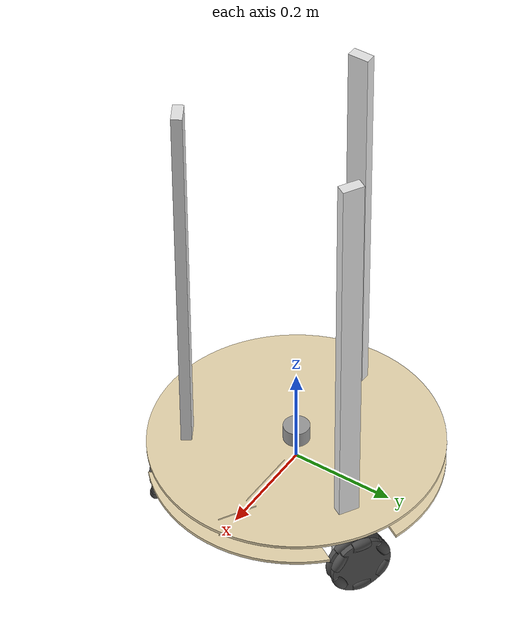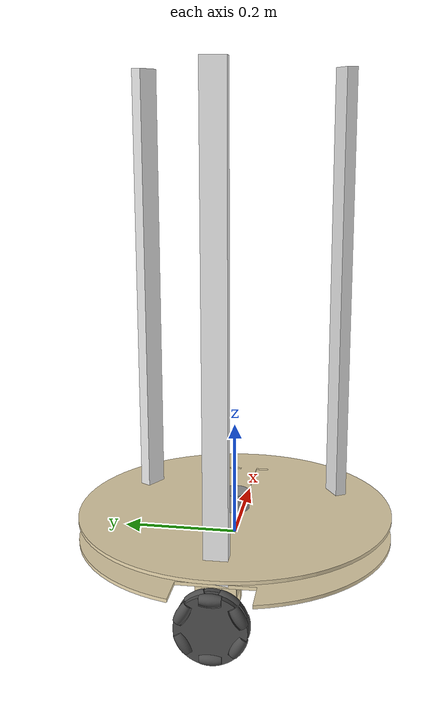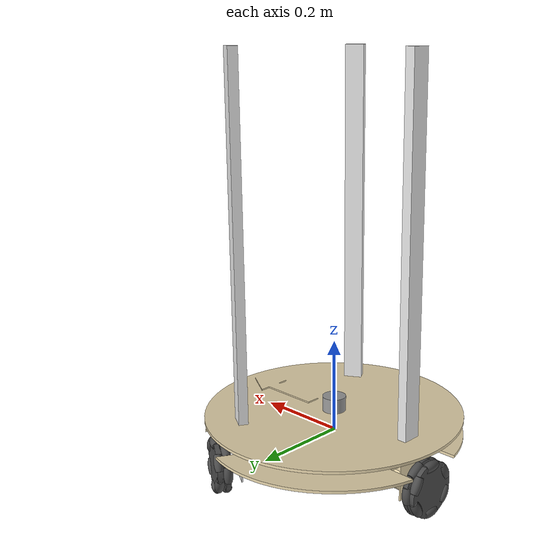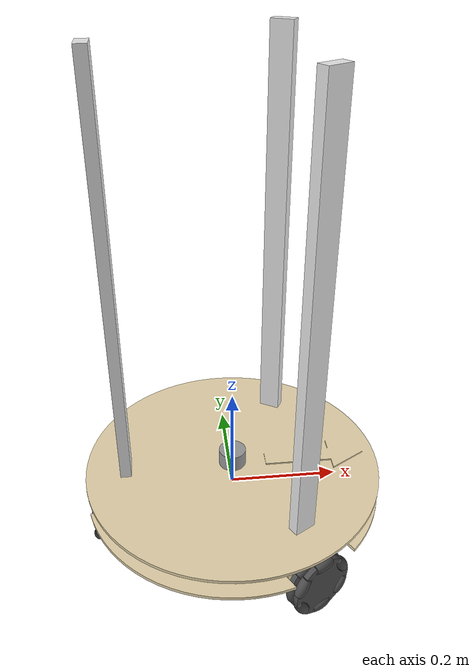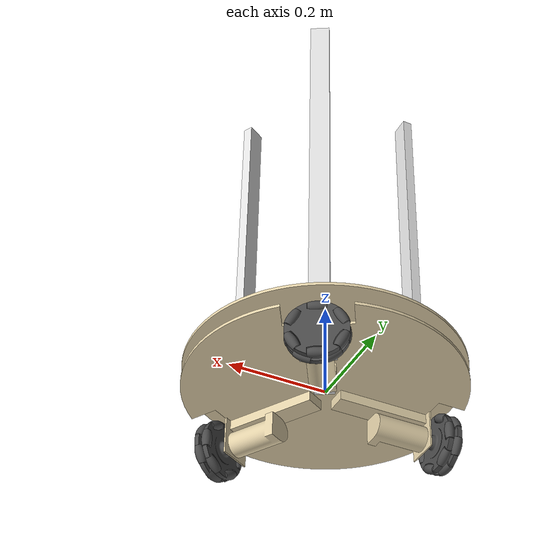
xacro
<?xml version="1.0"?>
<robot  name="robot" xmlns:xacro="http://www.ros.org/wiki/xacro">

    <xacro:include filename="$(find diffdrive_arduino)/ros2_control/diffbot.ros2_control.xacro"/>

    <joint name="base_footprint_to_base_link" type="fixed">
        <parent link="base_footprint" />
        <child link="base_link" />
        <origin rpy="0.0 0 0" xyz="0 0 0" />
    </joint>
    <link name="base_footprint"></link>

    <link name="base_link"></link>
    <joint name="base_link_to_base" type="fixed">
        <parent link="base_link" />
        <child link="base" />
        <origin rpy="0.0 0 1.57" xyz="0 0 0" />
    </joint>
    <link name="base">
        <visual>
            <origin xyz="0 0 0.036999999999999977351" rpy="0 -0 6.1232339957367660359e-17" />
            <geometry>
                <mesh filename="file://$(find omnicare_description)/meshes/omni/imu.stl" />
            </geometry>
            <material name="imu_material">
                <color rgba="0 0 1 0.6" />
            </material>
        </visual>
        <collision>
            <origin xyz="0 0 0.036999999999999977351" rpy="0 -0 6.1232339957367660359e-17" />
            <geometry>
                <mesh filename="file://$(find omnicare_description)/meshes/omni/imu.stl" />
            </geometry>
        </collision>
        <visual>
            <origin xyz="0 0 0.045999999999999985345" rpy="0 -0 6.1232339957367660359e-17" />
            <geometry>
                <mesh filename="file://$(find omnicare_description)/meshes/omni/lidar.stl" />
            </geometry>
            <material name="lidar_material">
                <color rgba="0.5999999999999999778 0.5999999999999999778 0.5999999999999999778 1.0" />
            </material>
        </visual>
        <collision>
            <origin xyz="0 0 0.045999999999999985345" rpy="0 -0 6.1232339957367660359e-17" />
            <geometry>
                <mesh filename="file://$(find omnicare_description)/meshes/omni/lidar.stl" />
            </geometry>
        </collision>
        <visual>
            <origin xyz="0 0.15507501269542200983 -0.045350000000000001421"
                rpy="0 -0 -3.141592653589793116" />
            <geometry>
                <mesh filename="file://$(find omnicare_description)/meshes/omni/motor.stl" />
            </geometry>
            <material name="motor_material">
                <color rgba="0.902 0.835 0.675 1" />
            </material>
        </visual>
        <collision>
            <origin xyz="0 0.15507501269542200983 -0.045350000000000001421"
                rpy="0 -0 -3.141592653589793116" />
            <geometry>
                <mesh filename="file://$(find omnicare_description)/meshes/omni/motor.stl" />
            </geometry>
        </collision>
        <visual>
            <origin xyz="0 0 0" rpy="0 -0 -1.570796326794896558" />
            <geometry>
                <mesh filename="file://$(find omnicare_description)/meshes/omni/mdf_motores.stl" />
            </geometry>
            <material name="mdf_motores_material">
                <color
                    rgba="0.902 0.835 0.675 1" />
            </material>
        </visual>
        <collision>
            <origin xyz="0 0 0" rpy="0 -0 -1.570796326794896558" />
            <geometry>
                <mesh filename="file://$(find omnicare_description)/meshes/omni/mdf_motores.stl" />
            </geometry>
        </collision>
        <visual>
            <origin xyz="0 0 0.039999999999999980016" rpy="0 -0 -1.570796326794896558" />
            <geometry>
                <mesh filename="file://$(find omnicare_description)/meshes/omni/mdf.stl" />
            </geometry>
            <material name="mdf_material">
                <color
                    rgba="0.902 0.835 0.675 1" />
            </material>
        </visual>
        <collision>
            <origin xyz="0 0 0.039999999999999980016" rpy="0 -0 -1.570796326794896558" />
            <geometry>
                <mesh filename="file://$(find omnicare_description)/meshes/omni/mdf.stl" />
            </geometry>
        </collision>
        <visual>
            <origin xyz="0 0.20737501269542202298 -0.010000000000000008882"
                rpy="0 -0 -3.141592653589793116" />
            <geometry>
                <mesh filename="file://$(find omnicare_description)/meshes/omni/perfil_motores.stl" />
            </geometry>
            <material name="perfil_motores_material">
                <color
                    rgba="0.902 0.835 0.675 1" />
            </material>
        </visual>
        <collision>
            <origin xyz="0 0.20737501269542202298 -0.010000000000000008882"
                rpy="0 -0 -3.141592653589793116" />
            <geometry>
                <mesh filename="file://$(find omnicare_description)/meshes/omni/perfil_motores.stl" />
            </geometry>
        </collision>
        <visual>
            <origin xyz="-0.17959202910435598244 -0.10368750634771095598 -0.010000000000000008882"
                rpy="0 -0 -1.0471975511965978534" />
            <geometry>
                <mesh filename="file://$(find omnicare_description)/meshes/omni/perfil_motores.stl" />
            </geometry>
            <material name="perfil_motores_material">
                <color
                    rgba="0.902 0.835 0.675 1" />
            </material>
        </visual>
        <collision>
            <origin xyz="-0.17959202910435598244 -0.10368750634771095598 -0.010000000000000008882"
                rpy="0 -0 -1.0471975511965978534" />
            <geometry>
                <mesh filename="file://$(find omnicare_description)/meshes/omni/perfil_motores.stl" />
            </geometry>
        </collision>
        <visual>
            <origin xyz="0.13429890048642970091 -0.077537506347710838384 -0.045350000000000001421"
                rpy="0 -0 1.0471975511965980754" />
            <geometry>
                <mesh filename="file://$(find omnicare_description)/meshes/omni/motor.stl" />
            </geometry>
            <material name="motor_material">
                <color rgba="0.902 0.835 0.675 1" />
            </material>
        </visual>
        <collision>
            <origin xyz="0.13429890048642970091 -0.077537506347710838384 -0.045350000000000001421"
                rpy="0 -0 1.0471975511965980754" />
            <geometry>
                <mesh filename="file://$(find omnicare_description)/meshes/omni/motor.stl" />
            </geometry>
        </collision>
        <visual>
            <origin xyz="-0.13429890048642978417 -0.077537506347710838384 -0.045350000000000001421"
                rpy="0 -0 -1.0471975511965978534" />
            <geometry>
                <mesh filename="file://$(find omnicare_description)/meshes/omni/motor.stl" />
            </geometry>
            <material name="motor_material">
                <color rgba="0.902 0.835 0.675 1" />
            </material>
        </visual>
        <collision>
            <origin xyz="-0.13429890048642978417 -0.077537506347710838384 -0.045350000000000001421"
                rpy="0 -0 -1.0471975511965978534" />
            <geometry>
                <mesh filename="file://$(find omnicare_description)/meshes/omni/motor.stl" />
            </geometry>
        </collision>
        <visual>
            <origin xyz="0 0.20037501269542201676 0.4000000000000000222"
                rpy="0 -0 -3.141592653589793116" />
            <geometry>
                <mesh filename="file://$(find omnicare_description)/meshes/omni/perfil_coluna.stl" />
            </geometry>
            <material name="perfil_coluna_material">
                <color
                    rgba="0.90196078431372550543 0.90196078431372550543 0.90196078431372550543 1.0" />
            </material>
        </visual>
        <collision>
            <origin xyz="0 0.20037501269542201676 0.4000000000000000222"
                rpy="0 -0 -3.141592653589793116" />
            <geometry>
                <mesh filename="file://$(find omnicare_description)/meshes/omni/perfil_coluna.stl" />
            </geometry>
        </collision>
        <visual>
            <origin xyz="0.17352985127786482722 -0.10018750634771089736 0.4000000000000000222"
                rpy="0 -0 1.0471975511965980754" />
            <geometry>
                <mesh filename="file://$(find omnicare_description)/meshes/omni/perfil_coluna.stl" />
            </geometry>
            <material name="perfil_coluna_material">
                <color
                    rgba="0.90196078431372550543 0.90196078431372550543 0.90196078431372550543 1.0" />
            </material>
        </visual>
        <collision>
            <origin xyz="0.17352985127786482722 -0.10018750634771089736 0.4000000000000000222"
                rpy="0 -0 1.0471975511965980754" />
            <geometry>
                <mesh filename="file://$(find omnicare_description)/meshes/omni/perfil_coluna.stl" />
            </geometry>
        </collision>
        <visual>
            <origin xyz="-0.17352985127786491049 -0.10018750634771089736 0.4000000000000000222"
                rpy="0 -0 -1.0471975511965978534" />
            <geometry>
                <mesh filename="file://$(find omnicare_description)/meshes/omni/perfil_coluna.stl" />
            </geometry>
            <material name="perfil_coluna_material">
                <color
                    rgba="0.90196078431372550543 0.90196078431372550543 0.90196078431372550543 1.0" />
            </material>
        </visual>
        <collision>
            <origin xyz="-0.17352985127786491049 -0.10018750634771089736 0.4000000000000000222"
                rpy="0 -0 -1.0471975511965978534" />
            <geometry>
                <mesh filename="file://$(find omnicare_description)/meshes/omni/perfil_coluna.stl" />
            </geometry>
        </collision>
        <visual>
            <origin xyz="0.17959202910435592693 -0.10368750634771095598 -0.010000000000000008882"
                rpy="0 -0 1.0471975511965980754" />
            <geometry>
                <mesh filename="file://$(find omnicare_description)/meshes/omni/perfil_motores.stl" />
            </geometry>
            <material name="perfil_motores_material">
                <color
                    rgba="0.90196078431372550543 0.90196078431372550543 0.90196078431372550543 1.0" />
            </material>
        </visual>
        <collision>
            <origin xyz="0.17959202910435592693 -0.10368750634771095598 -0.010000000000000008882"
                rpy="0 -0 1.0471975511965980754" />
            <geometry>
                <mesh filename="file://$(find omnicare_description)/meshes/omni/perfil_motores.stl" />
            </geometry>
        </collision>
        <inertial>
            <origin
                xyz="-2.5725654066226820008e-17 -0.00072713798642877675634 0.1130692369102963557"
                rpy="0 0 0" />
            <mass value="6.6083023665046667361" />
            <inertia ixx="0.44242217829366581316" ixy="-8.6736173798840354721e-18"
                ixz="-6.9388939039072283776e-18" iyy="0.44159185092185426758"
                iyz="-0.00042393505393957964938" izz="0.21274006069424275522" />
        </inertial>
    </link>

    <link name="roda">
        <visual>
            <origin xyz="2.2561951529011655937e-17 0 -0.03799999999999997824"
                rpy="1.570796326794896558 -6.586583941999015059e-17 0" />
            <geometry>
                <mesh filename="file://$(find omnicare_description)/meshes/omni/roda.stl" />
            </geometry>
            <material name="roda_material">
                <color
                    rgba="0.30196078431372547213 0.30196078431372547213 0.30196078431372547213 1.0" />
            </material>
        </visual>
        <collision>
            <origin xyz="2.2561951529011655937e-17 0 -0.03799999999999997824"
                rpy="1.570796326794896558 -6.586583941999015059e-17 0" />
            <geometry>
                <mesh filename="file://$(find omnicare_description)/meshes/omni/roda.stl" />
            </geometry>
        </collision>
        <inertial>
            <origin
                xyz="2.488178870261553677e-17 -5.0324958787843994577e-18 -0.036248827632811911337"
                rpy="0 0 0" />
            <mass value="0.17417946931200009586" />
            <inertia ixx="0.00011266723250859313221" ixy="0" ixz="1.9247504594027302389e-20"
                iyy="0.00011266723250859299668" iyz="0" izz="0.00018629763749933273714" />
        </inertial>
    </link>

    <link name="rolete">
        <visual>
            <origin xyz="0 8.6736173798840354721e-19 -0.017500000000000005135"
                rpy="1.570796326794896558 1.570796326794896558 0" />
            <geometry>
                <mesh filename="file://$(find omnicare_description)/meshes/omni/rolete.stl" />
            </geometry>
            <material name="rolete_material">
                <color
                    rgba="0.30196078431372547213 0.30196078431372547213 0.30196078431372547213 1.0" />
            </material>
        </visual>
        <collision>
            <origin xyz="0 8.6736173798840354721e-19 -0.017500000000000005135"
                rpy="1.570796326794896558 1.570796326794896558 0" />
            <geometry>
                <mesh filename="file://$(find omnicare_description)/meshes/omni/rolete.stl" />
            </geometry>
        </collision>
        <inertial>
            <origin
                xyz="-1.8827844672617356948e-33 8.8261553917125876786e-19 -0.017500000000000064115"
                rpy="0 0 0" />
            <mass value="0.0095254397280000006887" />
            <inertia ixx="1.036871279333562925e-06" ixy="0" ixz="4.8882119461100731892e-23"
                iyy="1.036871279333562925e-06" iyz="0" izz="4.2025448479089010245e-07" />
        </inertial>
    </link>

    <joint name="w1_external_1_passive" type="continuous">
        <origin xyz="0.01750000000000022024 -0.050000000000000002776 -0.046999999999999930722"
            rpy="-3.141592653589793116 -1.570796326794896558 0" />
        <parent link="roda" />
        <child link="rolete" />
        <axis xyz="0 0 1" />
        <limit effort="1" velocity="20" />
        <joint_properties friction="0.0" />
    </joint>

    <link name="rolete_2">
        <visual>
            <origin xyz="2.4286128663675299322e-17 0 -0.017499999999999994726"
                rpy="1.57079632679489678 1.570796326794896558 0" />
            <geometry>
                <mesh filename="file://$(find omnicare_description)/meshes/omni/rolete.stl" />
            </geometry>
            <material name="rolete_material">
                <color
                    rgba="0.30196078431372547213 0.30196078431372547213 0.30196078431372547213 1.0" />
            </material>
        </visual>
        <collision>
            <origin xyz="2.4286128663675299322e-17 0 -0.017499999999999994726"
                rpy="1.57079632679489678 1.570796326794896558 0" />
            <geometry>
                <mesh filename="file://$(find omnicare_description)/meshes/omni/rolete.stl" />
            </geometry>
        </collision>
        <inertial>
            <origin
                xyz="2.4286128663675299322e-17 1.5253801182852536392e-20 -0.017500000000000053707"
                rpy="0 0 0" />
            <mass value="0.0095254397280000006887" />
            <inertia ixx="1.036871279333562925e-06" ixy="-9.8521709296568722055e-23"
                ixz="4.5527875226217172078e-23" iyy="1.0368712793335625015e-06"
                iyz="1.2707801796025749803e-23" izz="4.2025448479088999657e-07" />
        </inertial>
    </link>

    <joint name="w1_external_2_passive" type="continuous">
        <origin xyz="0.052051270189221954254 -0.009844555433772231301 -0.047000000000000041744"
            rpy="1.570796326794896558 4.1633363423452281929e-17 2.6179938779914921909" />
        <parent link="roda" />
        <child link="rolete_2" />
        <axis xyz="0 0 1" />
        <limit effort="1" velocity="20" />
        <joint_properties friction="0.0" />
    </joint>

    <link name="rolete_3">
        <visual>
            <origin xyz="-5.5511151231257827021e-17 0 -0.017500000000000008604"
                rpy="1.570796326794896558 1.570796326794896558 0" />
            <geometry>
                <mesh filename="file://$(find omnicare_description)/meshes/omni/rolete.stl" />
            </geometry>
            <material name="rolete_material">
                <color
                    rgba="0.30196078431372547213 0.30196078431372547213 0.30196078431372547213 1.0" />
            </material>
        </visual>
        <collision>
            <origin xyz="-5.5511151231257827021e-17 0 -0.017500000000000008604"
                rpy="1.570796326794896558 1.570796326794896558 0" />
            <geometry>
                <mesh filename="file://$(find omnicare_description)/meshes/omni/rolete.stl" />
            </geometry>
        </collision>
        <inertial>
            <origin
                xyz="-5.5511151231257827021e-17 1.5253801182858512794e-20 -0.017500000000000067585"
                rpy="0 0 0" />
            <mass value="0.0095254397280000006887" />
            <inertia ixx="1.036871279333562925e-06" ixy="-1.1346483524460359774e-22"
                ixz="-4.9106517962622279409e-23" iyy="1.0368712793335625015e-06"
                iyz="-4.743476021288299381e-23" izz="4.2025448479088999657e-07" />
        </inertial>
    </link>

    <joint name="w1_external_3_passive" type="continuous">
        <origin xyz="0.052051270189221968132 0.0098445554337722868121 -0.047000000000000041744"
            rpy="-1.570796326794896558 4.163336342345265787e-17 -2.6179938779914921909" />
        <parent link="roda" />
        <child link="rolete_3" />
        <axis xyz="0 0 1" />
        <limit effort="1" velocity="20" />
        <joint_properties friction="0.0" />
    </joint>

    <link name="rolete_4">
        <visual>
            <origin xyz="0 0 -0.017500000000000005135"
                rpy="1.570796326794896558 1.570796326794896558 0" />
            <geometry>
                <mesh filename="file://$(find omnicare_description)/meshes/omni/rolete.stl" />
            </geometry>
            <material name="rolete_material">
                <color
                    rgba="0.30196078431372547213 0.30196078431372547213 0.30196078431372547213 1.0" />
            </material>
        </visual>
        <collision>
            <origin xyz="0 0 -0.017500000000000005135"
                rpy="1.570796326794896558 1.570796326794896558 0" />
            <geometry>
                <mesh filename="file://$(find omnicare_description)/meshes/omni/rolete.stl" />
            </geometry>
        </collision>
        <inertial>
            <origin
                xyz="-1.8827844672617356948e-33 1.5253801182855310935e-20 -0.017500000000000064115"
                rpy="0 0 0" />
            <mass value="0.0095254397280000006887" />
            <inertia ixx="1.036871279333562925e-06" ixy="0" ixz="4.8882119461100731892e-23"
                iyy="1.036871279333562925e-06" iyz="0" izz="4.2025448479089010245e-07" />
        </inertial>
    </link>

    <joint name="w1_external_4_passive" type="continuous">
        <origin xyz="0.01750000000000022024 0.050000000000000002776 -0.046999999999999930722"
            rpy="-3.141592653589793116 -1.570796326794896558 0" />
        <parent link="roda" />
        <child link="rolete_4" />
        <axis xyz="0 0 1" />
        <limit effort="1" velocity="20" />
        <joint_properties friction="0.0" />
    </joint>

    <link name="rolete_5">
        <visual>
            <origin
                xyz="2.7755575615628913511e-17 -5.5511151231257827021e-17 -0.017499999999999994726"
                rpy="1.570796326794896558 1.570796326794896558 0" />
            <geometry>
                <mesh filename="file://$(find omnicare_description)/meshes/omni/rolete.stl" />
            </geometry>
            <material name="rolete_material">
                <color
                    rgba="0.30196078431372547213 0.30196078431372547213 0.30196078431372547213 1.0" />
            </material>
        </visual>
        <collision>
            <origin
                xyz="2.7755575615628913511e-17 -5.5511151231257827021e-17 -0.017499999999999994726"
                rpy="1.570796326794896558 1.570796326794896558 0" />
            <geometry>
                <mesh filename="file://$(find omnicare_description)/meshes/omni/rolete.stl" />
            </geometry>
        </collision>
        <inertial>
            <origin
                xyz="2.7755575615628907348e-17 -5.5495897430074969875e-17 -0.017500000000000053707"
                rpy="0 0 0" />
            <mass value="0.0095254397280000006887" />
            <inertia ixx="1.0368712793335625015e-06" ixy="-4.0963790902128267643e-23"
                ixz="-1.0818296567685836479e-23" iyy="1.036871279333562925e-06"
                iyz="-6.588601138874492811e-23" izz="4.2025448479089010245e-07" />
        </inertial>
    </link>

    <joint name="w1_external_5_passive" type="continuous">
        <origin xyz="-0.034551270189221897078 0.040155444566227743719 -0.046999999999999930722"
            rpy="1.570796326794896558 9.7144514654709209156e-17 2.6179938779914921909" />
        <parent link="roda" />
        <child link="rolete_5" />
        <axis xyz="0 0 1" />
        <limit effort="1" velocity="20" />
        <joint_properties friction="0.0" />
    </joint>

    <link name="rolete_6">
        <visual>
            <origin xyz="-1.0408340855860842566e-17 0 -0.017500000000000001665"
                rpy="1.570796326794896558 1.570796326794896558 0" />
            <geometry>
                <mesh filename="file://$(find omnicare_description)/meshes/omni/rolete.stl" />
            </geometry>
            <material name="rolete_material">
                <color
                    rgba="0.30196078431372547213 0.30196078431372547213 0.30196078431372547213 1.0" />
            </material>
        </visual>
        <collision>
            <origin xyz="-1.0408340855860842566e-17 0 -0.017500000000000001665"
                rpy="1.570796326794896558 1.570796326794896558 0" />
            <geometry>
                <mesh filename="file://$(find omnicare_description)/meshes/omni/rolete.stl" />
            </geometry>
        </collision>
        <inertial>
            <origin
                xyz="-1.0408340855860839485e-17 1.5253801182855816492e-20 -0.017500000000000060646"
                rpy="0 0 0" />
            <mass value="0.0095254397280000006887" />
            <inertia ixx="1.036871279333562925e-06" ixy="-2.768231747198581055e-25"
                ixz="5.0706665674869720478e-23" iyy="1.0368712793335625015e-06"
                iyz="6.9838955980765615663e-24" izz="4.2025448479088999657e-07" />
        </inertial>
    </link>

    <joint name="w1_external_6_passive" type="continuous">
        <origin xyz="-0.034551270189221897078 -0.040155444566227743719 -0.046999999999999986233"
            rpy="-1.570796326794896558 4.163336342345242984e-17 -2.6179938779914930791" />
        <parent link="roda" />
        <child link="rolete_6" />
        <axis xyz="0 0 1" />
        <limit effort="1" velocity="20" />
        <joint_properties friction="0.0" />
    </joint>

    <link name="rolete_7">
        <visual>
            <origin
                xyz="-2.7755575615628913511e-17 6.9388939039072283776e-18 -0.017500000000000001665"
                rpy="1.57079632679489678 1.570796326794896558 0" />
            <geometry>
                <mesh filename="file://$(find omnicare_description)/meshes/omni/rolete.stl" />
            </geometry>
            <material name="rolete_material">
                <color
                    rgba="0.30196078431372547213 0.30196078431372547213 0.30196078431372547213 1.0" />
            </material>
        </visual>
        <collision>
            <origin
                xyz="-2.7755575615628913511e-17 6.9388939039072283776e-18 -0.017500000000000001665"
                rpy="1.57079632679489678 1.570796326794896558 0" />
            <geometry>
                <mesh filename="file://$(find omnicare_description)/meshes/omni/rolete.stl" />
            </geometry>
        </collision>
        <inertial>
            <origin
                xyz="-2.7755575615628907348e-17 6.954147705090087065e-18 -0.017500000000000060646"
                rpy="0 0 0" />
            <mass value="0.0095254397280000006887" />
            <inertia ixx="1.036871279333562925e-06" ixy="-9.1981940161177171789e-23"
                ixz="-7.5956770966860398685e-23" iyy="1.0368712793335625015e-06"
                iyz="-3.2944002181616020768e-23" izz="4.2025448479089010245e-07" />
        </inertial>
    </link>

    <joint name="w1_internal_1_passive" type="continuous">
        <origin xyz="0.0098445554337722885468 -0.052051270189221947315 -0.02899999999999994249"
            rpy="0.52359877559829937077 -1.570796326794896558 0" />
        <parent link="roda" />
        <child link="rolete_7" />
        <axis xyz="0 0 1" />
        <limit effort="1" velocity="20" />
        <joint_properties friction="0.0" />
    </joint>

    <link name="rolete_8">
        <visual>
            <origin
                xyz="-1.3877787807814456755e-17 -2.7755575615628913511e-17 -0.017499999999999984318"
                rpy="1.57079632679489678 1.570796326794896558 0" />
            <geometry>
                <mesh filename="file://$(find omnicare_description)/meshes/omni/rolete.stl" />
            </geometry>
            <material name="rolete_material">
                <color
                    rgba="0.30196078431372547213 0.30196078431372547213 0.30196078431372547213 1.0" />
            </material>
        </visual>
        <collision>
            <origin
                xyz="-1.3877787807814456755e-17 -2.7755575615628913511e-17 -0.017499999999999984318"
                rpy="1.57079632679489678 1.570796326794896558 0" />
            <geometry>
                <mesh filename="file://$(find omnicare_description)/meshes/omni/rolete.stl" />
            </geometry>
        </collision>
        <inertial>
            <origin
                xyz="-1.3877787807814456755e-17 -2.7740321814446059445e-17 -0.017500000000000043299"
                rpy="0 0 0" />
            <mass value="0.0095254397280000006887" />
            <inertia ixx="1.036871279333562925e-06" ixy="-1.5367233116820140911e-22" ixz="0"
                iyy="1.036871279333562925e-06" iyz="0" izz="4.2025448479089010245e-07" />
        </inertial>
    </link>

    <joint name="w1_internal_2_passive" type="continuous">
        <origin xyz="0.050000000000000016653 -0.017500000000000019013 -0.028999999999999970246"
            rpy="-1.570796326794896558 1.035468818874435832e-17 3.141592653589793116" />
        <parent link="roda" />
        <child link="rolete_8" />
        <axis xyz="0 0 1" />
        <limit effort="1" velocity="20" />
        <joint_properties friction="0.0" />
    </joint>

    <link name="rolete_9">
        <visual>
            <origin xyz="0 0 -0.017500000000000012074"
                rpy="1.570796326794896558 1.570796326794896558 0" />
            <geometry>
                <mesh filename="file://$(find omnicare_description)/meshes/omni/rolete.stl" />
            </geometry>
            <material name="rolete_material">
                <color
                    rgba="0.30196078431372547213 0.30196078431372547213 0.30196078431372547213 1.0" />
            </material>
        </visual>
        <collision>
            <origin xyz="0 0 -0.017500000000000012074"
                rpy="1.570796326794896558 1.570796326794896558 0" />
            <geometry>
                <mesh filename="file://$(find omnicare_description)/meshes/omni/rolete.stl" />
            </geometry>
        </collision>
        <inertial>
            <origin
                xyz="6.826351802735963352e-34 1.5253801182852948662e-20 -0.017500000000000071054"
                rpy="0 0 0" />
            <mass value="0.0095254397280000006887" />
            <inertia ixx="1.0368712793335625015e-06" ixy="6.320298096395906635e-23"
                ixz="5.2627960705977889939e-23" iyy="1.036871279333562925e-06"
                iyz="5.921319503369844075e-23" izz="4.2025448479089010245e-07" />
        </inertial>
    </link>

    <joint name="w1_internal_3_passive" type="continuous">
        <origin xyz="0.0098445554337722469135 0.052051270189221926499 -0.028999999999999998002"
            rpy="-0.5235987755982990377 -1.570796326794896558 0" />
        <parent link="roda" />
        <child link="rolete_9" />
        <axis xyz="0 0 1" />
        <limit effort="1" velocity="20" />
        <joint_properties friction="0.0" />
    </joint>

    <link name="rolete_10">
        <visual>
            <origin
                xyz="-2.7755575615628913511e-17 -1.3877787807814456755e-17 -0.017500000000000005135"
                rpy="1.570796326794896558 1.570796326794896336 0" />
            <geometry>
                <mesh filename="file://$(find omnicare_description)/meshes/omni/rolete.stl" />
            </geometry>
            <material name="rolete_material">
                <color
                    rgba="0.30196078431372547213 0.30196078431372547213 0.30196078431372547213 1.0" />
            </material>
        </visual>
        <collision>
            <origin
                xyz="-2.7755575615628913511e-17 -1.3877787807814456755e-17 -0.017500000000000005135"
                rpy="1.570796326794896558 1.570796326794896336 0" />
            <geometry>
                <mesh filename="file://$(find omnicare_description)/meshes/omni/rolete.stl" />
            </geometry>
        </collision>
        <inertial>
            <origin
                xyz="-2.7755575615628919674e-17 -1.3862534006631591905e-17 -0.017500000000000064115"
                rpy="0 0 0" />
            <mass value="0.0095254397280000006887" />
            <inertia ixx="1.036871279333562925e-06" ixy="-7.7910186758924711127e-24"
                ixz="2.8268114521713276342e-23" iyy="1.036871279333562925e-06"
                iyz="-8.6548165257709574266e-23" izz="4.2025448479088999657e-07" />
        </inertial>
    </link>

    <joint name="w1_internal_4_passive" type="continuous">
        <origin xyz="-0.0098445554337722486482 0.052051270189221954254 -0.028999999999999970246"
            rpy="-2.6179938779914890823 -1.570796326794896558 0" />
        <parent link="roda" />
        <child link="rolete_10" />
        <axis xyz="0 0 1" />
        <limit effort="1" velocity="20" />
        <joint_properties friction="0.0" />
    </joint>

    <link name="rolete_11">
        <visual>
            <origin xyz="0 0 -0.017500000000000001665"
                rpy="-1.570796326794896558 -1.570796326794896558 0" />
            <geometry>
                <mesh filename="file://$(find omnicare_description)/meshes/omni/rolete.stl" />
            </geometry>
            <material name="rolete_material">
                <color
                    rgba="0.30196078431372547213 0.30196078431372547213 0.30196078431372547213 1.0" />
            </material>
        </visual>
        <collision>
            <origin xyz="0 0 -0.017500000000000001665"
                rpy="-1.570796326794896558 -1.570796326794896558 0" />
            <geometry>
                <mesh filename="file://$(find omnicare_description)/meshes/omni/rolete.stl" />
            </geometry>
        </collision>
        <inertial>
            <origin
                xyz="2.0213337975787023887e-36 -1.5253801182855307926e-20 -0.017499999999999942685"
                rpy="0 0 0" />
            <mass value="0.0095254397280000006887" />
            <inertia ixx="1.0368712793335625015e-06" ixy="-1.5367233116820220845e-22"
                ixz="-7.1461093342603907888e-54" iyy="1.0368712793335625015e-06"
                iyz="4.1484128691436000634e-38" izz="4.2025448479089010245e-07" />
        </inertial>
    </link>

    <joint name="w1_internal_5_passive" type="continuous">
        <origin xyz="-0.049999999999999988898 -0.017500000000000001665 -0.028999999999999970246"
            rpy="-1.570796326794896558 6.5865839420001391858e-17 -3.1415926535897926719" />
        <parent link="roda" />
        <child link="rolete_11" />
        <axis xyz="0 0 1" />
        <limit effort="1" velocity="20" />
        <joint_properties friction="0.0" />
    </joint>

    <link name="rolete_12">
        <visual>
            <origin
                xyz="2.7755575615628913511e-17 6.9388939039072283776e-18 -0.017499999999999991257"
                rpy="-1.570796326794896558 -1.570796326794896558 0" />
            <geometry>
                <mesh filename="file://$(find omnicare_description)/meshes/omni/rolete.stl" />
            </geometry>
            <material name="rolete_material">
                <color
                    rgba="0.30196078431372547213 0.30196078431372547213 0.30196078431372547213 1.0" />
            </material>
        </visual>
        <collision>
            <origin
                xyz="2.7755575615628913511e-17 6.9388939039072283776e-18 -0.017499999999999991257"
                rpy="-1.570796326794896558 -1.570796326794896558 0" />
            <geometry>
                <mesh filename="file://$(find omnicare_description)/meshes/omni/rolete.stl" />
            </geometry>
        </collision>
        <inertial>
            <origin
                xyz="2.7755575615628913511e-17 6.9236401027243743125e-18 -0.017499999999999932276"
                rpy="0 0 0" />
            <mass value="0.0095254397280000006887" />
            <inertia ixx="1.0368712793335625015e-06" ixy="-6.320298096395906635e-23"
                ixz="-5.2627960705977889939e-23" iyy="1.036871279333562925e-06"
                iyz="5.921319503369844075e-23" izz="4.2025448479089010245e-07" />
        </inertial>
    </link>

    <joint name="w1_internal_6_passive" type="continuous">
        <origin xyz="-0.0098445554337722746691 -0.052051270189221933438 -0.028999999999999998002"
            rpy="2.6179938779914944114 -1.570796326794896558 0" />
        <parent link="roda" />
        <child link="rolete_12" />
        <axis xyz="0 0 1" />
        <limit effort="1" velocity="20" />
        <joint_properties friction="0.0" />
    </joint>

    <joint name="wheel1_speed" type="continuous">
        <origin xyz="-0.18305613071949367043 -0.10568750634771079122 -0.045350000000000001421"
            rpy="-1.570796326794896558 -0 -1.0471975511965978534" />
        <parent link="base" />
        <child link="roda" />
        <axis xyz="0 0 1" />
        <limit effort="1" velocity="20" />
        <joint_properties friction="0.1" />
    </joint>

    <link name="roda_2">
        <visual>
            <origin xyz="1.924008601513291951e-17 0 -0.038000000000000005995"
                rpy="1.570796326794896558 1.0888646801245511308e-17 0" />
            <geometry>
                <mesh filename="file://$(find omnicare_description)/meshes/omni/roda.stl" />
            </geometry>
            <material name="roda_material">
                <color
                    rgba="0.30196078431372547213 0.30196078431372547213 0.30196078431372547213 1.0" />
            </material>
        </visual>
        <collision>
            <origin xyz="1.924008601513291951e-17 0 -0.038000000000000005995"
                rpy="1.570796326794896558 1.0888646801245511308e-17 0" />
            <geometry>
                <mesh filename="file://$(find omnicare_description)/meshes/omni/roda.stl" />
            </geometry>
        </collision>
        <inertial>
            <origin
                xyz="2.1429687027549190121e-17 -5.0324958787843994577e-18 -0.036248827632811939092"
                rpy="0 0 0" />
            <mass value="0.17417946931200009586" />
            <inertia ixx="0.00011266723250859313221" ixy="0" ixz="-3.255322875496582062e-21"
                iyy="0.00011266723250859299668" iyz="0" izz="0.00018629763749933273714" />
        </inertial>
    </link>

    <link name="rolete_13">
        <visual>
            <origin xyz="0 0 -0.017499999999999998196"
                rpy="-1.570796326794896558 -1.570796326794896558 0" />
            <geometry>
                <mesh filename="file://$(find omnicare_description)/meshes/omni/rolete.stl" />
            </geometry>
            <material name="rolete_material">
                <color
                    rgba="0.30196078431372547213 0.30196078431372547213 0.30196078431372547213 1.0" />
            </material>
        </visual>
        <collision>
            <origin xyz="0 0 -0.017499999999999998196"
                rpy="-1.570796326794896558 -1.570796326794896558 0" />
            <geometry>
                <mesh filename="file://$(find omnicare_description)/meshes/omni/rolete.stl" />
            </geometry>
        </collision>
        <inertial>
            <origin
                xyz="-6.3314101991071797471e-34 -1.5253801182855310935e-20 -0.017499999999999939215"
                rpy="0 0 0" />
            <mass value="0.0095254397280000006887" />
            <inertia ixx="1.036871279333562925e-06" ixy="0" ixz="-1.5866127790546147935e-23"
                iyy="1.036871279333562925e-06" iyz="0" izz="4.2025448479089010245e-07" />
        </inertial>
    </link>

    <joint name="w2_external_1_passive" type="continuous">
        <origin xyz="0.017500000000000001665 -0.050000000000000002776 -0.046999999999999986233"
            rpy="-3.141592653589793116 -1.570796326794896558 0" />
        <parent link="roda_2" />
        <child link="rolete_13" />
        <axis xyz="0 0 1" />
        <limit effort="1" velocity="20" />
        <joint_properties friction="0.0" />
    </joint>

    <link name="rolete_14">
        <visual>
            <origin
                xyz="5.898059818321144121e-17 5.5511151231257827021e-17 -0.017500000000000015543"
                rpy="-1.570796326794896558 -1.570796326794896558 0" />
            <geometry>
                <mesh filename="file://$(find omnicare_description)/meshes/omni/rolete.stl" />
            </geometry>
            <material name="rolete_material">
                <color
                    rgba="0.30196078431372547213 0.30196078431372547213 0.30196078431372547213 1.0" />
            </material>
        </visual>
        <collision>
            <origin
                xyz="5.898059818321144121e-17 5.5511151231257827021e-17 -0.017500000000000015543"
                rpy="-1.570796326794896558 -1.570796326794896558 0" />
            <geometry>
                <mesh filename="file://$(find omnicare_description)/meshes/omni/rolete.stl" />
            </geometry>
        </collision>
        <inertial>
            <origin
                xyz="5.898059818321144121e-17 5.5495897430074969875e-17 -0.017499999999999956563"
                rpy="0 0 0" />
            <mass value="0.0095254397280000006887" />
            <inertia ixx="1.036871279333562925e-06" ixy="1.5828427558469117513e-22"
                ixz="-5.8001448433174275041e-23" iyy="1.036871279333562925e-06"
                iyz="-5.3480503937111131051e-23" izz="4.2025448479089010245e-07" />
        </inertial>
    </link>

    <joint name="w2_external_2_passive" type="continuous">
        <origin xyz="0.052051270189221961193 -0.0098445554337722798732 -0.046999999999999986233"
            rpy="-1.570796326794896558 8.3266726846886740532e-17 -0.52359877559829937077" />
        <parent link="roda_2" />
        <child link="rolete_14" />
        <axis xyz="0 0 1" />
        <limit effort="1" velocity="20" />
        <joint_properties friction="0.0" />
    </joint>

    <link name="rolete_15">
        <visual>
            <origin xyz="0 -5.5511151231257827021e-17 -0.017499999999999987788"
                rpy="-1.570796326794896558 -1.570796326794896558 0" />
            <geometry>
                <mesh filename="file://$(find omnicare_description)/meshes/omni/rolete.stl" />
            </geometry>
            <material name="rolete_material">
                <color
                    rgba="0.30196078431372547213 0.30196078431372547213 0.30196078431372547213 1.0" />
            </material>
        </visual>
        <collision>
            <origin xyz="0 -5.5511151231257827021e-17 -0.017499999999999987788"
                rpy="-1.570796326794896558 -1.570796326794896558 0" />
            <geometry>
                <mesh filename="file://$(find omnicare_description)/meshes/omni/rolete.stl" />
            </geometry>
        </collision>
        <inertial>
            <origin
                xyz="-6.2240683356283600417e-33 -5.5526405032440678005e-17 -0.017499999999999928807"
                rpy="0 0 0" />
            <mass value="0.0095254397280000006887" />
            <inertia ixx="1.0368712793335633485e-06" ixy="-1.0792109698955899103e-23"
                ixz="-3.6717742077867041247e-23" iyy="1.0368712793335633485e-06"
                iyz="-6.5360850930781627318e-23" izz="4.2025448479089010245e-07" />
        </inertial>
    </link>

    <joint name="w2_external_3_passive" type="continuous">
        <origin xyz="0.0345512701892218832 0.04015544456622767433 -0.046999999999999986233"
            rpy="-1.570796326794896558 -1.9428902930940232062e-16 0.5235987755982980385" />
        <parent link="roda_2" />
        <child link="rolete_15" />
        <axis xyz="0 0 1" />
        <limit effort="1" velocity="20" />
        <joint_properties friction="0.0" />
    </joint>

    <link name="rolete_16">
        <visual>
            <origin xyz="0 0 -0.017499999999999998196"
                rpy="-1.570796326794896558 -1.570796326794896558 0" />
            <geometry>
                <mesh filename="file://$(find omnicare_description)/meshes/omni/rolete.stl" />
            </geometry>
            <material name="rolete_material">
                <color
                    rgba="0.30196078431372547213 0.30196078431372547213 0.30196078431372547213 1.0" />
            </material>
        </visual>
        <collision>
            <origin xyz="0 0 -0.017499999999999998196"
                rpy="-1.570796326794896558 -1.570796326794896558 0" />
            <geometry>
                <mesh filename="file://$(find omnicare_description)/meshes/omni/rolete.stl" />
            </geometry>
        </collision>
        <inertial>
            <origin
                xyz="-6.3314101991071797471e-34 -1.5253801182855310935e-20 -0.017499999999999939215"
                rpy="0 0 0" />
            <mass value="0.0095254397280000006887" />
            <inertia ixx="1.036871279333562925e-06" ixy="0" ixz="-1.5866127790546147935e-23"
                iyy="1.036871279333562925e-06" iyz="0" izz="4.2025448479089010245e-07" />
        </inertial>
    </link>

    <joint name="w2_external_4_passive" type="continuous">
        <origin xyz="0.017500000000000001665 0.050000000000000002776 -0.046999999999999986233"
            rpy="-3.141592653589793116 -1.570796326794896558 0" />
        <parent link="roda_2" />
        <child link="rolete_16" />
        <axis xyz="0 0 1" />
        <limit effort="1" velocity="20" />
        <joint_properties friction="0.0" />
    </joint>

    <link name="rolete_17">
        <visual>
            <origin xyz="0 0 -0.017500000000000008604"
                rpy="-1.570796326794896558 -1.570796326794896558 0" />
            <geometry>
                <mesh filename="file://$(find omnicare_description)/meshes/omni/rolete.stl" />
            </geometry>
            <material name="rolete_material">
                <color
                    rgba="0.30196078431372547213 0.30196078431372547213 0.30196078431372547213 1.0" />
            </material>
        </visual>
        <collision>
            <origin xyz="0 0 -0.017500000000000008604"
                rpy="-1.570796326794896558 -1.570796326794896558 0" />
            <geometry>
                <mesh filename="file://$(find omnicare_description)/meshes/omni/rolete.stl" />
            </geometry>
        </collision>
        <inertial>
            <origin
                xyz="-7.954688526444711983e-33 -1.5253801182854994962e-20 -0.017499999999999949624"
                rpy="0 0 0" />
            <mass value="0.0095254397280000006887" />
            <inertia ixx="1.036871279333562925e-06" ixy="1.0072635719025811458e-22"
                ixz="-9.9619879685609982716e-23" iyy="1.036871279333562925e-06"
                iyz="4.0774144573219287677e-24" izz="4.2025448479089031421e-07" />
        </inertial>
    </link>

    <joint name="w2_external_5_passive" type="continuous">
        <origin xyz="-0.034551270189221931772 0.040155444566227688208 -0.047000000000000041744"
            rpy="-1.570796326794896558 2.7755575615628950488e-17 -0.5235987755982990377" />
        <parent link="roda_2" />
        <child link="rolete_17" />
        <axis xyz="0 0 1" />
        <limit effort="1" velocity="20" />
        <joint_properties friction="0.0" />
    </joint>

    <link name="rolete_18">
        <visual>
            <origin xyz="-1.7347234759768070944e-17 0 -0.017500000000000001665"
                rpy="-1.570796326794896558 -1.570796326794896558 0" />
            <geometry>
                <mesh filename="file://$(find omnicare_description)/meshes/omni/rolete.stl" />
            </geometry>
            <material name="rolete_material">
                <color
                    rgba="0.30196078431372547213 0.30196078431372547213 0.30196078431372547213 1.0" />
            </material>
        </visual>
        <collision>
            <origin xyz="-1.7347234759768070944e-17 0 -0.017500000000000001665"
                rpy="-1.570796326794896558 -1.570796326794896558 0" />
            <geometry>
                <mesh filename="file://$(find omnicare_description)/meshes/omni/rolete.stl" />
            </geometry>
        </collision>
        <inertial>
            <origin
                xyz="-1.7347234759768074026e-17 -1.5253801182856707234e-20 -0.017499999999999942685"
                rpy="0 0 0" />
            <mass value="0.0095254397280000006887" />
            <inertia ixx="1.036871279333562925e-06" ixy="-8.1586521587915913837e-24"
                ixz="4.6054875199953665828e-24" iyy="1.036871279333562925e-06"
                iyz="2.7566748423715992865e-24" izz="4.2025448479089010245e-07" />
        </inertial>
    </link>

    <joint name="w2_external_6_passive" type="continuous">
        <origin xyz="-0.052051270189221968132 -0.0098445554337723215066 -0.046999999999999986233"
            rpy="-1.570796326794896558 -2.4980018054065997508e-16 0.52359877559829848259" />
        <parent link="roda_2" />
        <child link="rolete_18" />
        <axis xyz="0 0 1" />
        <limit effort="1" velocity="20" />
        <joint_properties friction="0.0" />
    </joint>

    <link name="rolete_19">
        <visual>
            <origin xyz="0 1.7347234759768070944e-18 -0.017499999999999994726"
                rpy="1.570796326794896558 1.570796326794896558 0" />
            <geometry>
                <mesh filename="file://$(find omnicare_description)/meshes/omni/rolete.stl" />
            </geometry>
            <material name="rolete_material">
                <color
                    rgba="0.30196078431372547213 0.30196078431372547213 0.30196078431372547213 1.0" />
            </material>
        </visual>
        <collision>
            <origin xyz="0 1.7347234759768070944e-18 -0.017499999999999994726"
                rpy="1.570796326794896558 1.570796326794896558 0" />
            <geometry>
                <mesh filename="file://$(find omnicare_description)/meshes/omni/rolete.stl" />
            </geometry>
        </collision>
        <inertial>
            <origin
                xyz="-2.4207111105014599648e-33 1.7499772771596623151e-18 -0.017500000000000053707"
                rpy="0 0 0" />
            <mass value="0.0095254397280000006887" />
            <inertia ixx="1.036871279333562925e-06" ixy="-1.748883405819762942e-23"
                ixz="-2.5671831100193852867e-23" iyy="1.0368712793335625015e-06"
                iyz="-9.6151919207745793873e-24" izz="4.2025448479089010245e-07" />
        </inertial>
    </link>

    <joint name="w2_internal_1_passive" type="continuous">
        <origin xyz="0.0098445554337722798732 -0.052051270189221954254 -0.028999999999999998002"
            rpy="0.52359877559829937077 -1.570796326794896558 0" />
        <parent link="roda_2" />
        <child link="rolete_19" />
        <axis xyz="0 0 1" />
        <limit effort="1" velocity="20" />
        <joint_properties friction="0.0" />
    </joint>

    <link name="rolete_20">
        <visual>
            <origin
                xyz="1.3877787807814456755e-17 2.7755575615628913511e-17 -0.017500000000000001665"
                rpy="1.570796326794896558 1.570796326794896558 0" />
            <geometry>
                <mesh filename="file://$(find omnicare_description)/meshes/omni/rolete.stl" />
            </geometry>
            <material name="rolete_material">
                <color
                    rgba="0.30196078431372547213 0.30196078431372547213 0.30196078431372547213 1.0" />
            </material>
        </visual>
        <collision>
            <origin
                xyz="1.3877787807814456755e-17 2.7755575615628913511e-17 -0.017500000000000001665"
                rpy="1.570796326794896558 1.570796326794896558 0" />
            <geometry>
                <mesh filename="file://$(find omnicare_description)/meshes/omni/rolete.stl" />
            </geometry>
        </collision>
        <inertial>
            <origin
                xyz="1.3877787807814456755e-17 2.7770829416811770657e-17 -0.017500000000000060646"
                rpy="0 0 0" />
            <mass value="0.0095254397280000006887" />
            <inertia ixx="1.036871279333562925e-06" ixy="2.2580250278037481391e-23" ixz="0"
                iyy="1.036871279333562925e-06" iyz="0" izz="4.2025448479089010245e-07" />
        </inertial>
    </link>

    <joint name="w2_internal_2_passive" type="continuous">
        <origin xyz="0.050000000000000030531 0.017500000000000015543 -0.029000000000000025757"
            rpy="-1.570796326794896558 1.0888646801245511308e-17 0" />
        <parent link="roda_2" />
        <child link="rolete_20" />
        <axis xyz="0 0 1" />
        <limit effort="1" velocity="20" />
        <joint_properties friction="0.0" />
    </joint>

    <link name="rolete_21">
        <visual>
            <origin xyz="2.7755575615628913511e-17 0 -0.017499999999999998196"
                rpy="1.570796326794896558 1.570796326794896558 0" />
            <geometry>
                <mesh filename="file://$(find omnicare_description)/meshes/omni/rolete.stl" />
            </geometry>
            <material name="rolete_material">
                <color
                    rgba="0.30196078431372547213 0.30196078431372547213 0.30196078431372547213 1.0" />
            </material>
        </visual>
        <collision>
            <origin xyz="2.7755575615628913511e-17 0 -0.017499999999999998196"
                rpy="1.570796326794896558 1.570796326794896558 0" />
            <geometry>
                <mesh filename="file://$(find omnicare_description)/meshes/omni/rolete.stl" />
            </geometry>
        </collision>
        <inertial>
            <origin
                xyz="2.7755575615628919674e-17 1.5253801182858539877e-20 -0.017500000000000057176"
                rpy="0 0 0" />
            <mass value="0.0095254397280000006887" />
            <inertia ixx="1.036871279333562925e-06" ixy="1.748883405819797913e-23"
                ixz="-5.5214897555080703434e-23" iyy="1.036871279333562925e-06"
                iyz="-2.6907636523957872575e-23" izz="4.2025448479089031421e-07" />
        </inertial>
    </link>

    <joint name="w2_internal_3_passive" type="continuous">
        <origin xyz="0.0098445554337723163024 0.052051270189221954254 -0.028999999999999970246"
            rpy="-0.52359877559829870464 -1.570796326794896558 0" />
        <parent link="roda_2" />
        <child link="rolete_21" />
        <axis xyz="0 0 1" />
        <limit effort="1" velocity="20" />
        <joint_properties friction="0.0" />
    </joint>

    <link name="rolete_22">
        <visual>
            <origin xyz="2.7755575615628913511e-17 0 -0.017499999999999987788"
                rpy="1.570796326794896558 1.570796326794896558 0" />
            <geometry>
                <mesh filename="file://$(find omnicare_description)/meshes/omni/rolete.stl" />
            </geometry>
            <material name="rolete_material">
                <color
                    rgba="0.30196078431372547213 0.30196078431372547213 0.30196078431372547213 1.0" />
            </material>
        </visual>
        <collision>
            <origin xyz="2.7755575615628913511e-17 0 -0.017499999999999987788"
                rpy="1.570796326794896558 1.570796326794896558 0" />
            <geometry>
                <mesh filename="file://$(find omnicare_description)/meshes/omni/rolete.stl" />
            </geometry>
        </collision>
        <inertial>
            <origin
                xyz="2.7755575615628919674e-17 1.5253801182852081993e-20 -0.017500000000000046768"
                rpy="0 0 0" />
            <mass value="0.0095254397280000006887" />
            <inertia ixx="1.036871279333562925e-06" ixy="-1.748883405819797913e-23"
                ixz="-5.5214897555080703434e-23" iyy="1.036871279333562925e-06"
                iyz="2.6907636523957872575e-23" izz="4.2025448479089031421e-07" />
        </inertial>
    </link>

    <joint name="w2_internal_4_passive" type="continuous">
        <origin xyz="-0.040155444566227702086 0.034551270189221924833 -0.028999999999999998002"
            rpy="0.52359877559829870464 -1.570796326794896558 0" />
        <parent link="roda_2" />
        <child link="rolete_22" />
        <axis xyz="0 0 1" />
        <limit effort="1" velocity="20" />
        <joint_properties friction="0.0" />
    </joint>

    <link name="rolete_23">
        <visual>
            <origin
                xyz="1.3877787807814456755e-17 2.7755575615628913511e-17 -0.017500000000000001665"
                rpy="1.570796326794896558 1.570796326794896558 0" />
            <geometry>
                <mesh filename="file://$(find omnicare_description)/meshes/omni/rolete.stl" />
            </geometry>
            <material name="rolete_material">
                <color
                    rgba="0.30196078431372547213 0.30196078431372547213 0.30196078431372547213 1.0" />
            </material>
        </visual>
        <collision>
            <origin
                xyz="1.3877787807814456755e-17 2.7755575615628913511e-17 -0.017500000000000001665"
                rpy="1.570796326794896558 1.570796326794896558 0" />
            <geometry>
                <mesh filename="file://$(find omnicare_description)/meshes/omni/rolete.stl" />
            </geometry>
        </collision>
        <inertial>
            <origin
                xyz="1.3877787807814456755e-17 2.7770829416811770657e-17 -0.017500000000000060646"
                rpy="0 0 0" />
            <mass value="0.0095254397280000006887" />
            <inertia ixx="1.036871279333562925e-06" ixy="2.2580250278037481391e-23" ixz="0"
                iyy="1.036871279333562925e-06" iyz="0" izz="4.2025448479089010245e-07" />
        </inertial>
    </link>

    <joint name="w2_internal_5_passive" type="continuous">
        <origin xyz="-0.04999999999999997502 0.017500000000000029421 -0.029000000000000025757"
            rpy="-1.570796326794896558 1.0888646801245511308e-17 0" />
        <parent link="roda_2" />
        <child link="rolete_23" />
        <axis xyz="0 0 1" />
        <limit effort="1" velocity="20" />
        <joint_properties friction="0.0" />
    </joint>

    <link name="rolete_24">
        <visual>
            <origin
                xyz="-5.5511151231257827021e-17 -5.2041704279304212832e-18 -0.01749999999999997044"
                rpy="1.570796326794896558 1.570796326794896558 0" />
            <geometry>
                <mesh filename="file://$(find omnicare_description)/meshes/omni/rolete.stl" />
            </geometry>
            <material name="rolete_material">
                <color
                    rgba="0.30196078431372547213 0.30196078431372547213 0.30196078431372547213 1.0" />
            </material>
        </visual>
        <collision>
            <origin
                xyz="-5.5511151231257827021e-17 -5.2041704279304212832e-18 -0.01749999999999997044"
                rpy="1.570796326794896558 1.570796326794896558 0" />
            <geometry>
                <mesh filename="file://$(find omnicare_description)/meshes/omni/rolete.stl" />
            </geometry>
        </collision>
        <inertial>
            <origin
                xyz="-5.5511151231257827021e-17 -5.1889166267475702996e-18 -0.017500000000000029421"
                rpy="0 0 0" />
            <mass value="0.0095254397280000006887" />
            <inertia ixx="1.036871279333562925e-06" ixy="6.5029481368571926964e-23"
                ixz="2.1154315611014304178e-23" iyy="1.036871279333562925e-06"
                iyz="-4.049970058234187773e-23" izz="4.2025448479089010245e-07" />
        </inertial>
    </link>

    <joint name="w2_internal_6_passive" type="continuous">
        <origin xyz="-0.040155444566227702086 -0.034551270189221897078 -0.028999999999999998002"
            rpy="-0.52359877559829959282 -1.570796326794896558 0" />
        <parent link="roda_2" />
        <child link="rolete_24" />
        <axis xyz="0 0 1" />
        <limit effort="1" velocity="20" />
        <joint_properties friction="0.0" />
    </joint>

    <joint name="wheel3_speed" type="continuous">
        <origin xyz="0.18305613071949361492 -0.10568750634771083285 -0.045350000000000001421"
            rpy="-1.570796326794896558 -0 1.0471975511965980754" />
        <parent link="base" />
        <child link="roda_2" />
        <axis xyz="0 0 1" />
        <limit effort="1" velocity="20" />
        <joint_properties friction="0.1" />
    </joint>

    <link name="roda_3">
        <visual>
            <origin xyz="1.1275702593849246114e-17 0 -0.038000000000000005995"
                rpy="1.570796326794896558 -0 0" />
            <geometry>
                <mesh filename="file://$(find omnicare_description)/meshes/omni/roda.stl" />
            </geometry>
            <material name="roda_material">
                <color
                    rgba="0.30196078431372547213 0.30196078431372547213 0.30196078431372547213 1.0" />
            </material>
        </visual>
        <collision>
            <origin xyz="1.1275702593849246114e-17 0 -0.038000000000000005995"
                rpy="1.570796326794896558 -0 0" />
            <geometry>
                <mesh filename="file://$(find omnicare_description)/meshes/omni/roda.stl" />
            </geometry>
        </collision>
        <inertial>
            <origin
                xyz="1.3484371503659927598e-17 -5.0324958787843994577e-18 -0.036248827632811939092"
                rpy="0 0 0" />
            <mass value="0.17417946931200009586" />
            <inertia ixx="0.00011266723250859313221" ixy="0" ixz="0" iyy="0.00011266723250859299668"
                iyz="0" izz="0.00018629763749933273714" />
        </inertial>
    </link>

    <link name="rolete_25">
        <visual>
            <origin xyz="0 0 -0.017499999999999984318"
                rpy="1.570796326794896558 1.570796326794896558 0" />
            <geometry>
                <mesh filename="file://$(find omnicare_description)/meshes/omni/rolete.stl" />
            </geometry>
            <material name="rolete_material">
                <color
                    rgba="0.30196078431372547213 0.30196078431372547213 0.30196078431372547213 1.0" />
            </material>
        </visual>
        <collision>
            <origin xyz="0 0 -0.017499999999999984318"
                rpy="1.570796326794896558 1.570796326794896558 0" />
            <geometry>
                <mesh filename="file://$(find omnicare_description)/meshes/omni/rolete.stl" />
            </geometry>
        </collision>
        <inertial>
            <origin
                xyz="1.4649851994158461193e-50 1.5253801182855310935e-20 -0.017500000000000043299"
                rpy="0 0 0" />
            <mass value="0.0095254397280000006887" />
            <inertia ixx="1.036871279333562925e-06" ixy="0" ixz="0" iyy="1.036871279333562925e-06"
                iyz="0" izz="4.2025448479089010245e-07" />
        </inertial>
    </link>

    <joint name="w3_external_1_passive" type="continuous">
        <origin xyz="0.017500000000000008604 0.050000000000000002776 -0.046999999999999986233"
            rpy="-0 1.570796326794896558 0" />
        <parent link="roda_3" />
        <child link="rolete_25" />
        <axis xyz="0 0 1" />
        <limit effort="1" velocity="20" />
        <joint_properties friction="0.0" />
    </joint>

    <link name="rolete_26">
        <visual>
            <origin xyz="0 -3.4694469519536141888e-18 -0.017499999999999987788"
                rpy="1.570796326794896558 1.570796326794896558 0" />
            <geometry>
                <mesh filename="file://$(find omnicare_description)/meshes/omni/rolete.stl" />
            </geometry>
            <material name="rolete_material">
                <color
                    rgba="0.30196078431372547213 0.30196078431372547213 0.30196078431372547213 1.0" />
            </material>
        </visual>
        <collision>
            <origin xyz="0 -3.4694469519536141888e-18 -0.017499999999999987788"
                rpy="1.570796326794896558 1.570796326794896558 0" />
            <geometry>
                <mesh filename="file://$(find omnicare_description)/meshes/omni/rolete.stl" />
            </geometry>
        </collision>
        <inertial>
            <origin
                xyz="1.4649851994158461193e-50 -3.4541931507707620497e-18 -0.017500000000000046768"
                rpy="0 0 0" />
            <mass value="0.0095254397280000006887" />
            <inertia ixx="1.036871279333562925e-06" ixy="0" ixz="0" iyy="1.036871279333562925e-06"
                iyz="2.332881026084144285e-23" izz="4.2025448479089010245e-07" />
        </inertial>
    </link>

    <joint name="w3_external_2_passive" type="continuous">
        <origin xyz="-0.052051270189221926499 0.0098445554337723215066 -0.046999999999999986233"
            rpy="2.0943951023931952626 1.570796326794896558 0" />
        <parent link="roda_3" />
        <child link="rolete_26" />
        <axis xyz="0 0 1" />
        <limit effort="1" velocity="20" />
        <joint_properties friction="0.0" />
    </joint>

    <link name="rolete_27">
        <visual>
            <origin xyz="0 0 -0.017499999999999987788"
                rpy="1.570796326794896558 1.570796326794896558 0" />
            <geometry>
                <mesh filename="file://$(find omnicare_description)/meshes/omni/rolete.stl" />
            </geometry>
            <material name="rolete_material">
                <color
                    rgba="0.30196078431372547213 0.30196078431372547213 0.30196078431372547213 1.0" />
            </material>
        </visual>
        <collision>
            <origin xyz="0 0 -0.017499999999999987788"
                rpy="1.570796326794896558 1.570796326794896558 0" />
            <geometry>
                <mesh filename="file://$(find omnicare_description)/meshes/omni/rolete.stl" />
            </geometry>
        </collision>
        <inertial>
            <origin
                xyz="7.3098965278452823925e-49 1.5253801182860068584e-20 -0.017500000000000046768"
                rpy="0 0 0" />
            <mass value="0.0095254397280000006887" />
            <inertia ixx="1.036871279333562925e-06" ixy="-5.1121701000796439958e-38"
                ixz="-5.1800364577395554087e-39" iyy="1.036871279333562925e-06"
                iyz="-4.0885981298023131196e-24" izz="4.2025448479089010245e-07" />
        </inertial>
    </link>

    <joint name="w3_external_3_passive" type="continuous">
        <origin xyz="-0.034551270189221917895 -0.040155444566227688208 -0.046999999999999986233"
            rpy="1.0471975511965985195 1.570796326794896558 0" />
        <parent link="roda_3" />
        <child link="rolete_27" />
        <axis xyz="0 0 1" />
        <limit effort="1" velocity="20" />
        <joint_properties friction="0.0" />
    </joint>

    <link name="rolete_28">
        <visual>
            <origin xyz="0 0 -0.017499999999999984318"
                rpy="1.570796326794896558 1.570796326794896558 0" />
            <geometry>
                <mesh filename="file://$(find omnicare_description)/meshes/omni/rolete.stl" />
            </geometry>
            <material name="rolete_material">
                <color
                    rgba="0.30196078431372547213 0.30196078431372547213 0.30196078431372547213 1.0" />
            </material>
        </visual>
        <collision>
            <origin xyz="0 0 -0.017499999999999984318"
                rpy="1.570796326794896558 1.570796326794896558 0" />
            <geometry>
                <mesh filename="file://$(find omnicare_description)/meshes/omni/rolete.stl" />
            </geometry>
        </collision>
        <inertial>
            <origin
                xyz="1.4649851994158461193e-50 1.5253801182855310935e-20 -0.017500000000000043299"
                rpy="0 0 0" />
            <mass value="0.0095254397280000006887" />
            <inertia ixx="1.036871279333562925e-06" ixy="0" ixz="0" iyy="1.036871279333562925e-06"
                iyz="0" izz="4.2025448479089010245e-07" />
        </inertial>
    </link>

    <joint name="w3_external_4_passive" type="continuous">
        <origin xyz="0.017500000000000015543 -0.050000000000000002776 -0.046999999999999986233"
            rpy="-0 1.570796326794896558 0" />
        <parent link="roda_3" />
        <child link="rolete_28" />
        <axis xyz="0 0 1" />
        <limit effort="1" velocity="20" />
        <joint_properties friction="0.0" />
    </joint>

    <link name="rolete_29">
        <visual>
            <origin xyz="0 0 -0.017500000000000001665"
                rpy="1.570796326794896558 1.570796326794896558 0" />
            <geometry>
                <mesh filename="file://$(find omnicare_description)/meshes/omni/rolete.stl" />
            </geometry>
            <material name="rolete_material">
                <color
                    rgba="0.30196078431372547213 0.30196078431372547213 0.30196078431372547213 1.0" />
            </material>
        </visual>
        <collision>
            <origin xyz="0 0 -0.017500000000000001665"
                rpy="1.570796326794896558 1.570796326794896558 0" />
            <geometry>
                <mesh filename="file://$(find omnicare_description)/meshes/omni/rolete.stl" />
            </geometry>
        </collision>
        <inertial>
            <origin
                xyz="-8.1465871546058912604e-50 1.5253801182855942881e-20 -0.017500000000000060646"
                rpy="0 0 0" />
            <mass value="0.0095254397280000006887" />
            <inertia ixx="1.036871279333562925e-06" ixy="-2.5560850500398225199e-38"
                ixz="-2.6579109519949264715e-38" iyy="1.036871279333562925e-06"
                iyz="-1.5866127790546147935e-23" izz="4.2025448479089010245e-07" />
        </inertial>
    </link>

    <joint name="w3_external_5_passive" type="continuous">
        <origin xyz="0.034551270189221987283 -0.040155444566227646574 -0.047000000000000041744"
            rpy="2.0943951023931952626 1.570796326794896558 0" />
        <parent link="roda_3" />
        <child link="rolete_29" />
        <axis xyz="0 0 1" />
        <limit effort="1" velocity="20" />
        <joint_properties friction="0.0" />
    </joint>

    <link name="rolete_30">
        <visual>
            <origin xyz="0 -6.9388939039072283776e-18 -0.01749999999999997391"
                rpy="1.570796326794896558 1.570796326794896558 0" />
            <geometry>
                <mesh filename="file://$(find omnicare_description)/meshes/omni/rolete.stl" />
            </geometry>
            <material name="rolete_material">
                <color
                    rgba="0.30196078431372547213 0.30196078431372547213 0.30196078431372547213 1.0" />
            </material>
        </visual>
        <collision>
            <origin xyz="0 -6.9388939039072283776e-18 -0.01749999999999997391"
                rpy="1.570796326794896558 1.570796326794896558 0" />
            <geometry>
                <mesh filename="file://$(find omnicare_description)/meshes/omni/rolete.stl" />
            </geometry>
        </collision>
        <inertial>
            <origin
                xyz="1.4649851994158461193e-50 -6.9236401027243735422e-18 -0.01750000000000003289"
                rpy="0 0 0" />
            <mass value="0.0095254397280000006887" />
            <inertia ixx="1.036871279333562925e-06" ixy="0" ixz="0" iyy="1.036871279333562925e-06"
                iyz="5.8074058310303018972e-24" izz="4.2025448479089010245e-07" />
        </inertial>
    </link>

    <joint name="w3_external_6_passive" type="continuous">
        <origin xyz="0.052051270189221940377 0.0098445554337723562011 -0.047000000000000041744"
            rpy="1.0471975511965971872 1.570796326794896558 0" />
        <parent link="roda_3" />
        <child link="rolete_30" />
        <axis xyz="0 0 1" />
        <limit effort="1" velocity="20" />
        <joint_properties friction="0.0" />
    </joint>

    <link name="rolete_31">
        <visual>
            <origin xyz="0 -1.7347234759768070944e-18 -0.017499999999999998196"
                rpy="-1.570796326794896558 -1.570796326794896558 0" />
            <geometry>
                <mesh filename="file://$(find omnicare_description)/meshes/omni/rolete.stl" />
            </geometry>
            <material name="rolete_material">
                <color
                    rgba="0.30196078431372547213 0.30196078431372547213 0.30196078431372547213 1.0" />
            </material>
        </visual>
        <collision>
            <origin xyz="0 -1.7347234759768070944e-18 -0.017499999999999998196"
                rpy="-1.570796326794896558 -1.570796326794896558 0" />
            <geometry>
                <mesh filename="file://$(find omnicare_description)/meshes/omni/rolete.stl" />
            </geometry>
        </collision>
        <inertial>
            <origin
                xyz="-1.0633392247169934554e-48 -1.7499772771596630854e-18 -0.017499999999999939215"
                rpy="0 0 0" />
            <mass value="0.0095254397280000006887" />
            <inertia ixx="1.036871279333562925e-06" ixy="1.7122523123584191965e-39"
                ixz="-2.0519279954224318399e-38" iyy="1.036871279333562925e-06"
                iyz="-3.6542485023711619518e-23" izz="4.2025448479089010245e-07" />
        </inertial>
    </link>

    <joint name="w3_internal_1_passive" type="continuous">
        <origin xyz="-0.04015544456622767433 0.034551270189221938711 -0.028999999999999998002"
            rpy="2.6179938779914944114 1.570796326794896558 0" />
        <parent link="roda_3" />
        <child link="rolete_31" />
        <axis xyz="0 0 1" />
        <limit effort="1" velocity="20" />
        <joint_properties friction="0.0" />
    </joint>

    <link name="rolete_32">
        <visual>
            <origin xyz="0 0 -0.017499999999999994726"
                rpy="-1.570796326794896558 -1.570796326794896558 0" />
            <geometry>
                <mesh filename="file://$(find omnicare_description)/meshes/omni/rolete.stl" />
            </geometry>
            <material name="rolete_material">
                <color
                    rgba="0.30196078431372547213 0.30196078431372547213 0.30196078431372547213 1.0" />
            </material>
        </visual>
        <collision>
            <origin xyz="0 0 -0.017499999999999994726"
                rpy="-1.570796326794896558 -1.570796326794896558 0" />
            <geometry>
                <mesh filename="file://$(find omnicare_description)/meshes/omni/rolete.stl" />
            </geometry>
        </collision>
        <inertial>
            <origin
                xyz="1.4649851994158461193e-50 -1.5253801182855310935e-20 -0.017499999999999935746"
                rpy="0 0 0" />
            <mass value="0.0095254397280000006887" />
            <inertia ixx="1.036871279333562925e-06" ixy="0" ixz="0" iyy="1.036871279333562925e-06"
                iyz="0" izz="4.2025448479089010245e-07" />
        </inertial>
    </link>

    <joint name="w3_internal_2_passive" type="continuous">
        <origin xyz="-0.049999999999999995837 -0.017500000000000001665 -0.028999999999999998002"
            rpy="1.5707963267948961139 1.570796326794896558 0" />
        <parent link="roda_3" />
        <child link="rolete_32" />
        <axis xyz="0 0 1" />
        <limit effort="1" velocity="20" />
        <joint_properties friction="0.0" />
    </joint>

    <link name="rolete_33">
        <visual>
            <origin xyz="0 1.3877787807814456755e-17 -0.017500000000000008604"
                rpy="-1.570796326794896558 -1.570796326794896558 0" />
            <geometry>
                <mesh filename="file://$(find omnicare_description)/meshes/omni/rolete.stl" />
            </geometry>
            <material name="rolete_material">
                <color
                    rgba="0.30196078431372547213 0.30196078431372547213 0.30196078431372547213 1.0" />
            </material>
        </visual>
        <collision>
            <origin xyz="0 1.3877787807814456755e-17 -0.017500000000000008604"
                rpy="-1.570796326794896558 -1.570796326794896558 0" />
            <geometry>
                <mesh filename="file://$(find omnicare_description)/meshes/omni/rolete.stl" />
            </geometry>
        </collision>
        <inertial>
            <origin
                xyz="-7.0524817847406287909e-49 1.3862534006631601149e-17 -0.017499999999999949624"
                rpy="0 0 0" />
            <mass value="0.0095254397280000006887" />
            <inertia ixx="1.036871279333562925e-06" ixy="1.5277531698818174387e-38"
                ixz="-8.567680222382662956e-39" iyy="1.036871279333562925e-06"
                iyz="9.6008023062592710903e-24" izz="4.2025448479089010245e-07" />
        </inertial>
    </link>

    <joint name="w3_internal_3_passive" type="continuous">
        <origin xyz="-0.040155444566227702086 -0.0345512701892218832 -0.029000000000000025757"
            rpy="-2.6179938779914930791 1.570796326794896558 0" />
        <parent link="roda_3" />
        <child link="rolete_33" />
        <axis xyz="0 0 1" />
        <limit effort="1" velocity="20" />
        <joint_properties friction="0.0" />
    </joint>

    <link name="rolete_34">
        <visual>
            <origin xyz="0 0 -0.017499999999999998196"
                rpy="-1.570796326794896558 -1.570796326794896558 0" />
            <geometry>
                <mesh filename="file://$(find omnicare_description)/meshes/omni/rolete.stl" />
            </geometry>
            <material name="rolete_material">
                <color
                    rgba="0.30196078431372547213 0.30196078431372547213 0.30196078431372547213 1.0" />
            </material>
        </visual>
        <collision>
            <origin xyz="0 0 -0.017499999999999998196"
                rpy="-1.570796326794896558 -1.570796326794896558 0" />
            <geometry>
                <mesh filename="file://$(find omnicare_description)/meshes/omni/rolete.stl" />
            </geometry>
        </collision>
        <inertial>
            <origin
                xyz="7.3122804956860513409e-49 -1.5253801182855539639e-20 -0.017499999999999939215"
                rpy="0 0 0" />
            <mass value="0.0095254397280000006887" />
            <inertia ixx="1.036871279333562925e-06" ixy="2.3848598188039628841e-38"
                ixz="-1.2101761673599995861e-39" iyy="1.0368712793335625015e-06"
                iyz="5.1750512563402907797e-23" izz="4.2025448479089031421e-07" />
        </inertial>
    </link>

    <joint name="w3_internal_4_passive" type="continuous">
        <origin xyz="0.0098445554337722677302 -0.052051270189221940377 -0.028999999999999998002"
            rpy="2.6179938779914939673 1.570796326794896558 0" />
        <parent link="roda_3" />
        <child link="rolete_34" />
        <axis xyz="0 0 1" />
        <limit effort="1" velocity="20" />
        <joint_properties friction="0.0" />
    </joint>

    <link name="rolete_35">
        <visual>
            <origin xyz="0 0 -0.017500000000000001665"
                rpy="-1.570796326794896558 -1.570796326794896558 0" />
            <geometry>
                <mesh filename="file://$(find omnicare_description)/meshes/omni/rolete.stl" />
            </geometry>
            <material name="rolete_material">
                <color
                    rgba="0.30196078431372547213 0.30196078431372547213 0.30196078431372547213 1.0" />
            </material>
        </visual>
        <collision>
            <origin xyz="0 0 -0.017500000000000001665"
                rpy="-1.570796326794896558 -1.570796326794896558 0" />
            <geometry>
                <mesh filename="file://$(find omnicare_description)/meshes/omni/rolete.stl" />
            </geometry>
        </collision>
        <inertial>
            <origin
                xyz="1.4649851994158461193e-50 -1.5253801182855310935e-20 -0.017499999999999942685"
                rpy="0 0 0" />
            <mass value="0.0095254397280000006887" />
            <inertia ixx="1.036871279333562925e-06" ixy="0" ixz="0" iyy="1.036871279333562925e-06"
                iyz="0" izz="4.2025448479089010245e-07" />
        </inertial>
    </link>

    <joint name="w3_internal_5_passive" type="continuous">
        <origin xyz="0.050000000000000009714 -0.017500000000000015543 -0.029000000000000025757"
            rpy="1.570796326794896558 -0 0" />
        <parent link="roda_3" />
        <child link="rolete_35" />
        <axis xyz="0 0 1" />
        <limit effort="1" velocity="20" />
        <joint_properties friction="0.0" />
    </joint>

    <link name="rolete_36">
        <visual>
            <origin
                xyz="-2.7755575615628913511e-17 -1.7347234759768070944e-18 -0.017500000000000001665"
                rpy="-1.570796326794896558 -1.570796326794896558 0" />
            <geometry>
                <mesh filename="file://$(find omnicare_description)/meshes/omni/rolete.stl" />
            </geometry>
            <material name="rolete_material">
                <color
                    rgba="0.30196078431372547213 0.30196078431372547213 0.30196078431372547213 1.0" />
            </material>
        </visual>
        <collision>
            <origin
                xyz="-2.7755575615628913511e-17 -1.7347234759768070944e-18 -0.017500000000000001665"
                rpy="-1.570796326794896558 -1.570796326794896558 0" />
            <geometry>
                <mesh filename="file://$(find omnicare_description)/meshes/omni/rolete.stl" />
            </geometry>
        </collision>
        <inertial>
            <origin
                xyz="-2.7755575615628913511e-17 -1.7499772771596615447e-18 -0.017499999999999942685"
                rpy="0 0 0" />
            <mass value="0.0095254397280000006887" />
            <inertia ixx="1.036871279333562925e-06" ixy="1.7122523123589382844e-39"
                ixz="2.6212182114540462907e-39" iyy="1.036871279333562925e-06"
                iyz="3.6542485023711619518e-23" izz="4.2025448479089010245e-07" />
        </inertial>
    </link>

    <joint name="w3_internal_6_passive" type="continuous">
        <origin xyz="0.0098445554337723284455 0.052051270189221940377 -0.028999999999999998002"
            rpy="-2.6179938779914944114 1.570796326794896558 0" />
        <parent link="roda_3" />
        <child link="rolete_36" />
        <axis xyz="0 0 1" />
        <limit effort="1" velocity="20" />
        <joint_properties friction="0.0" />
    </joint>

    <joint name="wheel2_speed" type="continuous">
        <origin xyz="-1.1855237896668746136e-17 0.21137501269542202653 -0.045350000000000001421"
            rpy="1.570796326794896558 -0 2.1057260917706475226e-16" />
        <parent link="base" />
        <child link="roda_3" />
        <axis xyz="0 0 1" />
        <limit effort="1" velocity="20" />
        <joint_properties friction="0.1" />
    </joint>
</robot>
